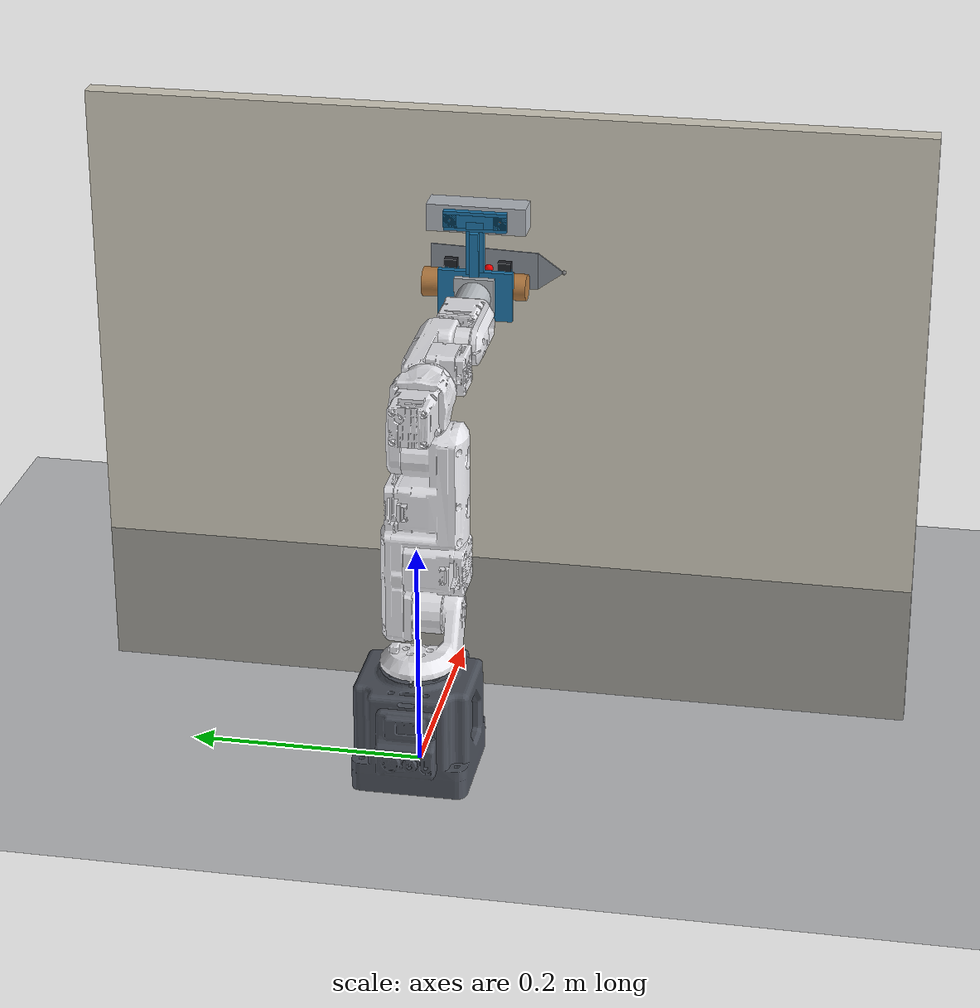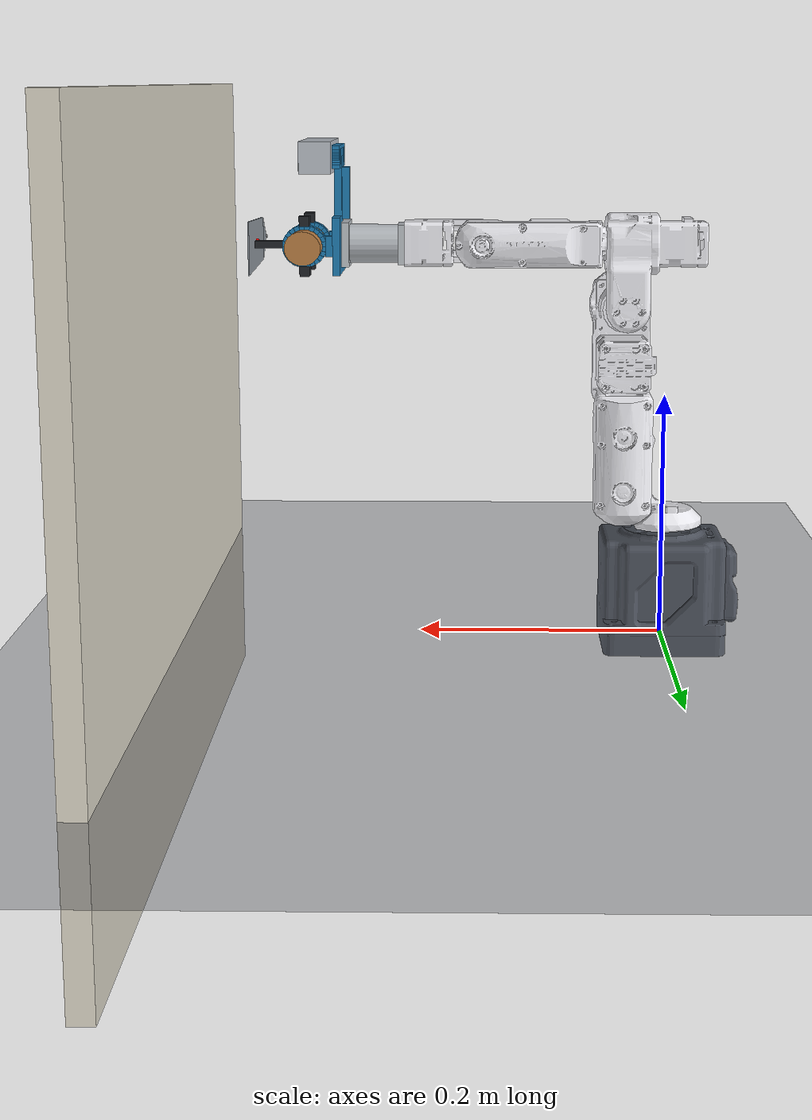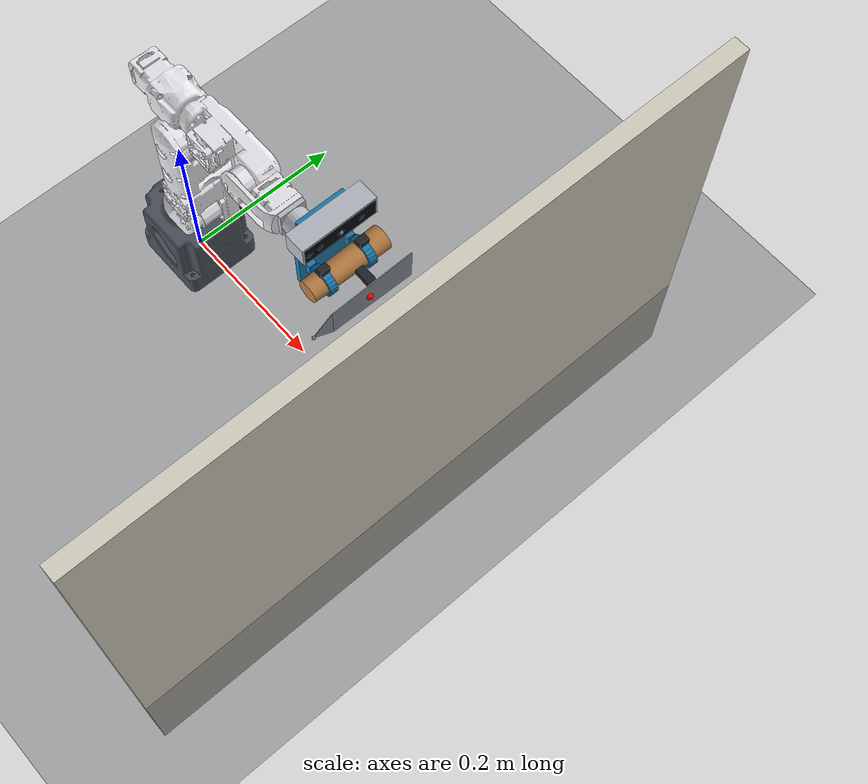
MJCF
<mujoco model="dummy_wall_trowel_SIM_ASSUMPTIONS_NOT_CALIBRATED">
  <!-- 由 tools/modeling/build_dummy_v2.py 生成，请勿手改。运动学 = V2 固件 DH；质量/惯量 = CAD 体积×估计密度 + 资料质量；执行器 = 资料额定值推算。均未经实机辨识。 -->
  <compiler angle="radian" meshdir="../../models/meshes_v2/" boundinertia="1e-07"/>

  <option integrator="implicitfast"/>

  <visual>
    <global offwidth="960" offheight="720"/>
  </visual>

  <default>
    <geom contype="0" conaffinity="0"/>
  </default>

  <asset>
    <mesh name="base_link" file="base_link.stl" scale="0.001 0.001 0.001" inertia="shell"/>
    <mesh name="link1" file="link1.stl" scale="0.001 0.001 0.001" inertia="shell"/>
    <mesh name="link2" file="link2.stl" scale="0.001 0.001 0.001" inertia="shell"/>
    <mesh name="link3" file="link3.stl" scale="0.001 0.001 0.001" inertia="shell"/>
    <mesh name="link4" file="link4.stl" scale="0.001 0.001 0.001" inertia="shell"/>
    <mesh name="link5" file="link5.stl" scale="0.001 0.001 0.001" inertia="shell"/>
    <mesh name="link6" file="link6.stl" scale="0.001 0.001 0.001" inertia="shell"/>
    <mesh name="handle_geom_mesh" vertex="0.0426612 0.041 0 0.0426612 0.0408909 0.00156631 0.0426612 0.0405656 0.00310583 0.0426612 0.0400295 0.0045922 0.0426612 0.0392918 0.006 0.0426612 0.0383653 0.00730514 0.0426612 0.0372656 0.00848528 0.0426612 0.0360117 0.00952024 0.0426612 0.034625 0.0103923 0.0426612 0.0331292 0.0110866 0.0426612 0.0315499 0.0115911 0.0426612 0.0299142 0.0118973 0.0426612 0.02825 0.012 0.0426612 0.0265858 0.0118973 0.0426612 0.0249501 0.0115911 0.0426612 0.0233708 0.0110866 0.0426612 0.021875 0.0103923 0.0426612 0.0204883 0.00952024 0.0426612 0.0192344 0.00848528 0.0426612 0.0181347 0.00730514 0.0426612 0.0172082 0.006 0.0426612 0.0164705 0.0045922 0.0426612 0.0159344 0.00310583 0.0426612 0.0156091 0.00156631 0.0426612 0.0155 1.46958e-18 0.0426612 0.0156091 -0.00156631 0.0426612 0.0159344 -0.00310583 0.0426612 0.0164705 -0.0045922 0.0426612 0.0172082 -0.006 0.0426612 0.0181347 -0.00730514 0.0426612 0.0192344 -0.00848528 0.0426612 0.0204883 -0.00952024 0.0426612 0.021875 -0.0103923 0.0426612 0.0233708 -0.0110866 0.0426612 0.0249501 -0.0115911 0.0426612 0.0265858 -0.0118973 0.0426612 0.02825 -0.012 0.0426612 0.0299142 -0.0118973 0.0426612 0.0315499 -0.0115911 0.0426612 0.0331292 -0.0110866 0.0426612 0.034625 -0.0103923 0.0426612 0.0360117 -0.00952024 0.0426612 0.0372656 -0.00848528 0.0426612 0.0383653 -0.00730514 0.0426612 0.0392918 -0.006 0.0426612 0.0400295 -0.0045922 0.0426612 0.0405656 -0.00310583 0.0426612 0.0408909 -0.00156631 -0.0523388 0.0425 0 -0.0523388 0.0423781 0.00172947 -0.0523388 0.0420144 0.00342935 -0.0523388 0.0414153 0.00507056 -0.0523388 0.0405909 0.006625 -0.0523388 0.0395553 0.00806609 -0.0523388 0.0383263 0.00936916 -0.0523388 0.0369249 0.0105119 -0.0523388 0.035375 0.0114748 -0.0523388 0.0337032 0.0122414 -0.0523388 0.0319382 0.0127985 -0.0523388 0.03011 0.0131366 -0.0523388 0.02825 0.01325 -0.0523388 0.02639 0.0131366 -0.0523388 0.0245618 0.0127985 -0.0523388 0.0227968 0.0122414 -0.0523388 0.021125 0.0114748 -0.0523388 0.0195751 0.0105119 -0.0523388 0.0181737 0.00936916 -0.0523388 0.0169447 0.00806609 -0.0523388 0.0159091 0.006625 -0.0523388 0.0150847 0.00507056 -0.0523388 0.0144856 0.00342935 -0.0523388 0.0141219 0.00172947 -0.0523388 0.014 1.62266e-18 -0.0523388 0.0141219 -0.00172947 -0.0523388 0.0144856 -0.00342935 -0.0523388 0.0150847 -0.00507056 -0.0523388 0.0159091 -0.006625 -0.0523388 0.0169447 -0.00806609 -0.0523388 0.0181737 -0.00936916 -0.0523388 0.0195751 -0.0105119 -0.0523388 0.021125 -0.0114748 -0.0523388 0.0227968 -0.0122414 -0.0523388 0.0245618 -0.0127985 -0.0523388 0.02639 -0.0131366 -0.0523388 0.02825 -0.01325 -0.0523388 0.03011 -0.0131366 -0.0523388 0.0319382 -0.0127985 -0.0523388 0.0337032 -0.0122414 -0.0523388 0.035375 -0.0114748 -0.0523388 0.0369249 -0.0105119 -0.0523388 0.0383263 -0.00936916 -0.0523388 0.0395553 -0.00806609 -0.0523388 0.0405909 -0.006625 -0.0523388 0.0414153 -0.00507056 -0.0523388 0.0420144 -0.00342935 -0.0523388 0.0423781 -0.00172947"/>
    <mesh name="clamp_0_0_mesh" vertex="-0.0315 0.0423999 0 -0.0315 0.0419178 0.00342071 -0.0315 0.0458999 0 -0.0315 0.0452985 0.00432657 -0.0225 0.0423999 0 -0.0225 0.0419178 0.00342071 -0.0225 0.0458999 0 -0.0225 0.0452985 0.00432657"/>
    <mesh name="clamp_0_1_mesh" vertex="-0.0315 0.0419178 0.00342071 -0.0315 0.0405042 0.0066083 -0.0315 0.0452985 0.00432657 -0.0315 0.0435353 0.0083583 -0.0225 0.0419178 0.00342071 -0.0225 0.0405042 0.0066083 -0.0225 0.0452985 0.00432657 -0.0225 0.0435353 0.0083583"/>
    <mesh name="clamp_0_2_mesh" vertex="-0.0315 0.0405042 0.0066083 -0.0315 0.0382555 0.00934554 -0.0315 0.0435353 0.0083583 -0.0315 0.0407304 0.0118204 -0.0225 0.0405042 0.0066083 -0.0225 0.0382555 0.00934554 -0.0225 0.0435353 0.0083583 -0.0225 0.0407304 0.0118204"/>
    <mesh name="clamp_0_3_mesh" vertex="-0.0315 0.0382555 0.00934554 -0.0315 0.035325 0.0114459 -0.0315 0.0407304 0.0118204 -0.0315 0.037075 0.014477 -0.0225 0.0382555 0.00934554 -0.0225 0.035325 0.0114459 -0.0225 0.0407304 0.0118204 -0.0225 0.037075 0.014477"/>
    <mesh name="clamp_0_4_mesh" vertex="-0.0315 0.035325 0.0114459 -0.0315 0.0319123 0.0127663 -0.0315 0.037075 0.014477 -0.0315 0.0328181 0.016147 -0.0225 0.035325 0.0114459 -0.0225 0.0319123 0.0127663 -0.0225 0.037075 0.014477 -0.0225 0.0328181 0.016147"/>
    <mesh name="clamp_0_5_mesh" vertex="-0.0315 0.0319123 0.0127663 -0.0315 0.0284198 0.0132156 -0.0315 0.0328181 0.016147 -0.0315 0.0284618 0.0167154 -0.0225 0.0319123 0.0127663 -0.0225 0.0284198 0.0132156 -0.0225 0.0328181 0.016147 -0.0225 0.0284618 0.0167154"/>
    <mesh name="clamp_0_6_mesh" vertex="-0.0315 0.0280802 0.0132156 -0.0315 0.0245877 0.0127663 -0.0315 0.0280382 0.0167154 -0.0315 0.0236819 0.016147 -0.0225 0.0280802 0.0132156 -0.0225 0.0245877 0.0127663 -0.0225 0.0280382 0.0167154 -0.0225 0.0236819 0.016147"/>
    <mesh name="clamp_0_7_mesh" vertex="-0.0315 0.0245877 0.0127663 -0.0315 0.021175 0.0114459 -0.0315 0.0236819 0.016147 -0.0315 0.019425 0.014477 -0.0225 0.0245877 0.0127663 -0.0225 0.021175 0.0114459 -0.0225 0.0236819 0.016147 -0.0225 0.019425 0.014477"/>
    <mesh name="clamp_0_8_mesh" vertex="-0.0315 0.021175 0.0114459 -0.0315 0.0182445 0.00934554 -0.0315 0.019425 0.014477 -0.0315 0.0157696 0.0118204 -0.0225 0.021175 0.0114459 -0.0225 0.0182445 0.00934554 -0.0225 0.019425 0.014477 -0.0225 0.0157696 0.0118204"/>
    <mesh name="clamp_0_9_mesh" vertex="-0.0315 0.0182445 0.00934554 -0.0315 0.0159958 0.0066083 -0.0315 0.0157696 0.0118204 -0.0315 0.0129647 0.0083583 -0.0225 0.0182445 0.00934554 -0.0225 0.0159958 0.0066083 -0.0225 0.0157696 0.0118204 -0.0225 0.0129647 0.0083583"/>
    <mesh name="clamp_0_10_mesh" vertex="-0.0315 0.0159958 0.0066083 -0.0315 0.0145822 0.00342071 -0.0315 0.0129647 0.0083583 -0.0315 0.0112015 0.00432657 -0.0225 0.0159958 0.0066083 -0.0225 0.0145822 0.00342071 -0.0225 0.0129647 0.0083583 -0.0225 0.0112015 0.00432657"/>
    <mesh name="clamp_0_11_mesh" vertex="-0.0315 0.0145822 0.00342071 -0.0315 0.0141001 1.61857e-18 -0.0315 0.0112015 0.00432657 -0.0315 0.0106001 2.04719e-18 -0.0225 0.0145822 0.00342071 -0.0225 0.0141001 1.61857e-18 -0.0225 0.0112015 0.00432657 -0.0225 0.0106001 2.04719e-18"/>
    <mesh name="clamp_0_12_mesh" vertex="-0.0315 0.0141001 1.61857e-18 -0.0315 0.0145822 -0.00342071 -0.0315 0.0106001 2.04719e-18 -0.0315 0.0112015 -0.00432657 -0.0225 0.0141001 1.61857e-18 -0.0225 0.0145822 -0.00342071 -0.0225 0.0106001 2.04719e-18 -0.0225 0.0112015 -0.00432657"/>
    <mesh name="clamp_0_13_mesh" vertex="-0.0315 0.0145822 -0.00342071 -0.0315 0.0159958 -0.0066083 -0.0315 0.0112015 -0.00432657 -0.0315 0.0129647 -0.0083583 -0.0225 0.0145822 -0.00342071 -0.0225 0.0159958 -0.0066083 -0.0225 0.0112015 -0.00432657 -0.0225 0.0129647 -0.0083583"/>
    <mesh name="clamp_0_14_mesh" vertex="-0.0315 0.0159958 -0.0066083 -0.0315 0.0182445 -0.00934554 -0.0315 0.0129647 -0.0083583 -0.0315 0.0157696 -0.0118204 -0.0225 0.0159958 -0.0066083 -0.0225 0.0182445 -0.00934554 -0.0225 0.0129647 -0.0083583 -0.0225 0.0157696 -0.0118204"/>
    <mesh name="clamp_0_15_mesh" vertex="-0.0315 0.0182445 -0.00934554 -0.0315 0.021175 -0.0114459 -0.0315 0.0157696 -0.0118204 -0.0315 0.019425 -0.014477 -0.0225 0.0182445 -0.00934554 -0.0225 0.021175 -0.0114459 -0.0225 0.0157696 -0.0118204 -0.0225 0.019425 -0.014477"/>
    <mesh name="clamp_0_16_mesh" vertex="-0.0315 0.021175 -0.0114459 -0.0315 0.0245877 -0.0127663 -0.0315 0.019425 -0.014477 -0.0315 0.0236819 -0.016147 -0.0225 0.021175 -0.0114459 -0.0225 0.0245877 -0.0127663 -0.0225 0.019425 -0.014477 -0.0225 0.0236819 -0.016147"/>
    <mesh name="clamp_0_17_mesh" vertex="-0.0315 0.0245877 -0.0127663 -0.0315 0.0280802 -0.0132156 -0.0315 0.0236819 -0.016147 -0.0315 0.0280382 -0.0167154 -0.0225 0.0245877 -0.0127663 -0.0225 0.0280802 -0.0132156 -0.0225 0.0236819 -0.016147 -0.0225 0.0280382 -0.0167154"/>
    <mesh name="clamp_0_18_mesh" vertex="-0.0315 0.0284198 -0.0132156 -0.0315 0.0319123 -0.0127663 -0.0315 0.0284618 -0.0167154 -0.0315 0.0328181 -0.016147 -0.0225 0.0284198 -0.0132156 -0.0225 0.0319123 -0.0127663 -0.0225 0.0284618 -0.0167154 -0.0225 0.0328181 -0.016147"/>
    <mesh name="clamp_0_19_mesh" vertex="-0.0315 0.0319123 -0.0127663 -0.0315 0.035325 -0.0114459 -0.0315 0.0328181 -0.016147 -0.0315 0.037075 -0.014477 -0.0225 0.0319123 -0.0127663 -0.0225 0.035325 -0.0114459 -0.0225 0.0328181 -0.016147 -0.0225 0.037075 -0.014477"/>
    <mesh name="clamp_0_20_mesh" vertex="-0.0315 0.035325 -0.0114459 -0.0315 0.0382555 -0.00934554 -0.0315 0.037075 -0.014477 -0.0315 0.0407304 -0.0118204 -0.0225 0.035325 -0.0114459 -0.0225 0.0382555 -0.00934554 -0.0225 0.037075 -0.014477 -0.0225 0.0407304 -0.0118204"/>
    <mesh name="clamp_0_21_mesh" vertex="-0.0315 0.0382555 -0.00934554 -0.0315 0.0405042 -0.0066083 -0.0315 0.0407304 -0.0118204 -0.0315 0.0435353 -0.0083583 -0.0225 0.0382555 -0.00934554 -0.0225 0.0405042 -0.0066083 -0.0225 0.0407304 -0.0118204 -0.0225 0.0435353 -0.0083583"/>
    <mesh name="clamp_0_22_mesh" vertex="-0.0315 0.0405042 -0.0066083 -0.0315 0.0419178 -0.00342071 -0.0315 0.0435353 -0.0083583 -0.0315 0.0452985 -0.00432657 -0.0225 0.0405042 -0.0066083 -0.0225 0.0419178 -0.00342071 -0.0225 0.0435353 -0.0083583 -0.0225 0.0452985 -0.00432657"/>
    <mesh name="clamp_0_23_mesh" vertex="-0.0315 0.0419178 -0.00342071 -0.0315 0.0423999 -3.23713e-18 -0.0315 0.0452985 -0.00432657 -0.0315 0.0458999 -4.09438e-18 -0.0225 0.0419178 -0.00342071 -0.0225 0.0423999 -3.23713e-18 -0.0225 0.0452985 -0.00432657 -0.0225 0.0458999 -4.09438e-18"/>
    <mesh name="clamp_1_0_mesh" vertex="0.0175 0.0416262 0 0.0175 0.0411704 0.00325384 0.0175 0.0451262 0 0.0175 0.0445512 0.0041597 0.0265 0.0416262 0 0.0265 0.0411704 0.00325384 0.0265 0.0451262 0 0.0265 0.0445512 0.0041597"/>
    <mesh name="clamp_1_1_mesh" vertex="0.0175 0.0411704 0.00325384 0.0175 0.0398342 0.00628593 0.0175 0.0445512 0.0041597 0.0175 0.0428652 0.00803593 0.0265 0.0411704 0.00325384 0.0265 0.0398342 0.00628593 0.0265 0.0445512 0.0041597 0.0265 0.0428652 0.00803593"/>
    <mesh name="clamp_1_2_mesh" vertex="0.0175 0.0398342 0.00628593 0.0175 0.0377084 0.00888965 0.0175 0.0428652 0.00803593 0.0175 0.0401833 0.0113645 0.0265 0.0398342 0.00628593 0.0265 0.0377084 0.00888965 0.0265 0.0428652 0.00803593 0.0265 0.0401833 0.0113645"/>
    <mesh name="clamp_1_3_mesh" vertex="0.0175 0.0377084 0.00888965 0.0175 0.0349381 0.0108875 0.0175 0.0401833 0.0113645 0.0175 0.0366881 0.0139186 0.0265 0.0377084 0.00888965 0.0265 0.0349381 0.0108875 0.0265 0.0401833 0.0113645 0.0265 0.0366881 0.0139186"/>
    <mesh name="clamp_1_4_mesh" vertex="0.0175 0.0349381 0.0108875 0.0175 0.031712 0.0121435 0.0175 0.0366881 0.0139186 0.0175 0.0326179 0.0155242 0.0265 0.0349381 0.0108875 0.0265 0.031712 0.0121435 0.0265 0.0366881 0.0139186 0.0265 0.0326179 0.0155242"/>
    <mesh name="clamp_1_5_mesh" vertex="0.0175 0.031712 0.0121435 0.0175 0.0284105 0.012571 0.0175 0.0326179 0.0155242 0.0175 0.0284525 0.0160707 0.0265 0.031712 0.0121435 0.0265 0.0284105 0.012571 0.0265 0.0326179 0.0155242 0.0265 0.0284525 0.0160707"/>
    <mesh name="clamp_1_6_mesh" vertex="0.0175 0.0280895 0.012571 0.0175 0.024788 0.0121435 0.0175 0.0280475 0.0160707 0.0175 0.0238821 0.0155242 0.0265 0.0280895 0.012571 0.0265 0.024788 0.0121435 0.0265 0.0280475 0.0160707 0.0265 0.0238821 0.0155242"/>
    <mesh name="clamp_1_7_mesh" vertex="0.0175 0.024788 0.0121435 0.0175 0.0215619 0.0108875 0.0175 0.0238821 0.0155242 0.0175 0.0198119 0.0139186 0.0265 0.024788 0.0121435 0.0265 0.0215619 0.0108875 0.0265 0.0238821 0.0155242 0.0265 0.0198119 0.0139186"/>
    <mesh name="clamp_1_8_mesh" vertex="0.0175 0.0215619 0.0108875 0.0175 0.0187916 0.00888965 0.0175 0.0198119 0.0139186 0.0175 0.0163167 0.0113645 0.0265 0.0215619 0.0108875 0.0265 0.0187916 0.00888965 0.0265 0.0198119 0.0139186 0.0265 0.0163167 0.0113645"/>
    <mesh name="clamp_1_9_mesh" vertex="0.0175 0.0187916 0.00888965 0.0175 0.0166658 0.00628593 0.0175 0.0163167 0.0113645 0.0175 0.0136348 0.00803593 0.0265 0.0187916 0.00888965 0.0265 0.0166658 0.00628593 0.0265 0.0163167 0.0113645 0.0265 0.0136348 0.00803593"/>
    <mesh name="clamp_1_10_mesh" vertex="0.0175 0.0166658 0.00628593 0.0175 0.0153296 0.00325384 0.0175 0.0136348 0.00803593 0.0175 0.0119488 0.0041597 0.0265 0.0166658 0.00628593 0.0265 0.0153296 0.00325384 0.0265 0.0136348 0.00803593 0.0265 0.0119488 0.0041597"/>
    <mesh name="clamp_1_11_mesh" vertex="0.0175 0.0153296 0.00325384 0.0175 0.0148738 1.53961e-18 0.0175 0.0119488 0.0041597 0.0175 0.0113738 1.96823e-18 0.0265 0.0153296 0.00325384 0.0265 0.0148738 1.53961e-18 0.0265 0.0119488 0.0041597 0.0265 0.0113738 1.96823e-18"/>
    <mesh name="clamp_1_12_mesh" vertex="0.0175 0.0148738 1.53961e-18 0.0175 0.0153296 -0.00325384 0.0175 0.0113738 1.96823e-18 0.0175 0.0119488 -0.0041597 0.0265 0.0148738 1.53961e-18 0.0265 0.0153296 -0.00325384 0.0265 0.0113738 1.96823e-18 0.0265 0.0119488 -0.0041597"/>
    <mesh name="clamp_1_13_mesh" vertex="0.0175 0.0153296 -0.00325384 0.0175 0.0166658 -0.00628593 0.0175 0.0119488 -0.0041597 0.0175 0.0136348 -0.00803593 0.0265 0.0153296 -0.00325384 0.0265 0.0166658 -0.00628593 0.0265 0.0119488 -0.0041597 0.0265 0.0136348 -0.00803593"/>
    <mesh name="clamp_1_14_mesh" vertex="0.0175 0.0166658 -0.00628593 0.0175 0.0187916 -0.00888965 0.0175 0.0136348 -0.00803593 0.0175 0.0163167 -0.0113645 0.0265 0.0166658 -0.00628593 0.0265 0.0187916 -0.00888965 0.0265 0.0136348 -0.00803593 0.0265 0.0163167 -0.0113645"/>
    <mesh name="clamp_1_15_mesh" vertex="0.0175 0.0187916 -0.00888965 0.0175 0.0215619 -0.0108875 0.0175 0.0163167 -0.0113645 0.0175 0.0198119 -0.0139186 0.0265 0.0187916 -0.00888965 0.0265 0.0215619 -0.0108875 0.0265 0.0163167 -0.0113645 0.0265 0.0198119 -0.0139186"/>
    <mesh name="clamp_1_16_mesh" vertex="0.0175 0.0215619 -0.0108875 0.0175 0.024788 -0.0121435 0.0175 0.0198119 -0.0139186 0.0175 0.0238821 -0.0155242 0.0265 0.0215619 -0.0108875 0.0265 0.024788 -0.0121435 0.0265 0.0198119 -0.0139186 0.0265 0.0238821 -0.0155242"/>
    <mesh name="clamp_1_17_mesh" vertex="0.0175 0.024788 -0.0121435 0.0175 0.0280895 -0.012571 0.0175 0.0238821 -0.0155242 0.0175 0.0280475 -0.0160707 0.0265 0.024788 -0.0121435 0.0265 0.0280895 -0.012571 0.0265 0.0238821 -0.0155242 0.0265 0.0280475 -0.0160707"/>
    <mesh name="clamp_1_18_mesh" vertex="0.0175 0.0284105 -0.012571 0.0175 0.031712 -0.0121435 0.0175 0.0284525 -0.0160707 0.0175 0.0326179 -0.0155242 0.0265 0.0284105 -0.012571 0.0265 0.031712 -0.0121435 0.0265 0.0284525 -0.0160707 0.0265 0.0326179 -0.0155242"/>
    <mesh name="clamp_1_19_mesh" vertex="0.0175 0.031712 -0.0121435 0.0175 0.0349381 -0.0108875 0.0175 0.0326179 -0.0155242 0.0175 0.0366881 -0.0139186 0.0265 0.031712 -0.0121435 0.0265 0.0349381 -0.0108875 0.0265 0.0326179 -0.0155242 0.0265 0.0366881 -0.0139186"/>
    <mesh name="clamp_1_20_mesh" vertex="0.0175 0.0349381 -0.0108875 0.0175 0.0377084 -0.00888965 0.0175 0.0366881 -0.0139186 0.0175 0.0401833 -0.0113645 0.0265 0.0349381 -0.0108875 0.0265 0.0377084 -0.00888965 0.0265 0.0366881 -0.0139186 0.0265 0.0401833 -0.0113645"/>
    <mesh name="clamp_1_21_mesh" vertex="0.0175 0.0377084 -0.00888965 0.0175 0.0398342 -0.00628593 0.0175 0.0401833 -0.0113645 0.0175 0.0428652 -0.00803593 0.0265 0.0377084 -0.00888965 0.0265 0.0398342 -0.00628593 0.0265 0.0401833 -0.0113645 0.0265 0.0428652 -0.00803593"/>
    <mesh name="clamp_1_22_mesh" vertex="0.0175 0.0398342 -0.00628593 0.0175 0.0411704 -0.00325384 0.0175 0.0428652 -0.00803593 0.0175 0.0445512 -0.0041597 0.0265 0.0398342 -0.00628593 0.0265 0.0411704 -0.00325384 0.0265 0.0428652 -0.00803593 0.0265 0.0445512 -0.0041597"/>
    <mesh name="clamp_1_23_mesh" vertex="0.0175 0.0411704 -0.00325384 0.0175 0.0416262 -3.07922e-18 0.0175 0.0445512 -0.0041597 0.0175 0.0451262 -3.93647e-18 0.0265 0.0411704 -0.00325384 0.0265 0.0416262 -3.07922e-18 0.0265 0.0445512 -0.0041597 0.0265 0.0451262 -3.93647e-18"/>
    <mesh name="blade_geom_mesh" vertex="-0.0543388 0 -0.021 0.0456612 0 -0.0175 0.0456612 0 0.0175 -0.0543388 0 0.021 -0.0543388 0.001 -0.021 0.0456612 0.001 -0.0175 0.0456612 0.001 0.0175 -0.0543388 0.001 0.021"/>
    <mesh name="blade_tip_geom_mesh" vertex="0.0456612 0 -0.0175 0.0696612 0 0 0.0456612 0 0.0175 0.0456612 0.001 -0.0175 0.0696612 0.001 0 0.0456612 0.001 0.0175"/>
    <mesh name="camera_bore_0_0_mesh" vertex="-0.0209 0 0.07 -0.0209307 0 0.0703121 -0.0165 0 0.07 -0.0165 0 0.0711935 -0.0209 0.006 0.07 -0.0209307 0.006 0.0703121 -0.0165 0.006 0.07 -0.0165 0.006 0.0711935"/>
    <mesh name="camera_bore_0_1_mesh" vertex="-0.0209307 0 0.0703121 -0.0210218 0 0.0706123 -0.0165 0 0.0711935 -0.0165 0 0.0724853 -0.0209307 0.006 0.0703121 -0.0210218 0.006 0.0706123 -0.0165 0.006 0.0711935 -0.0165 0.006 0.0724853"/>
    <mesh name="camera_bore_0_2_mesh" vertex="-0.0210218 0 0.0706123 -0.0211696 0 0.0708889 -0.0165 0 0.0724853 -0.0165 0 0.0740091 -0.0210218 0.006 0.0706123 -0.0211696 0.006 0.0708889 -0.0165 0.006 0.0724853 -0.0165 0.006 0.0740091"/>
    <mesh name="camera_bore_0_3_mesh" vertex="-0.0211696 0 0.0708889 -0.0213686 0 0.0711314 -0.0165 0 0.0740091 -0.0165 0 0.076 -0.0211696 0.006 0.0708889 -0.0213686 0.006 0.0711314 -0.0165 0.006 0.0740091 -0.0165 0.006 0.076"/>
    <mesh name="camera_bore_0_4_mesh" vertex="-0.0213686 0 0.0711314 -0.0216111 0 0.0713304 -0.0165 0 0.076 -0.0184909 0 0.076 -0.0213686 0.006 0.0711314 -0.0216111 0.006 0.0713304 -0.0165 0.006 0.076 -0.0184909 0.006 0.076"/>
    <mesh name="camera_bore_0_5_mesh" vertex="-0.0216111 0 0.0713304 -0.0218877 0 0.0714782 -0.0184909 0 0.076 -0.0200147 0 0.076 -0.0216111 0.006 0.0713304 -0.0218877 0.006 0.0714782 -0.0184909 0.006 0.076 -0.0200147 0.006 0.076"/>
    <mesh name="camera_bore_0_6_mesh" vertex="-0.0218877 0 0.0714782 -0.0221879 0 0.0715693 -0.0200147 0 0.076 -0.0213065 0 0.076 -0.0218877 0.006 0.0714782 -0.0221879 0.006 0.0715693 -0.0200147 0.006 0.076 -0.0213065 0.006 0.076"/>
    <mesh name="camera_bore_0_7_mesh" vertex="-0.0221879 0 0.0715693 -0.0225 0 0.0716 -0.0213065 0 0.076 -0.0225 0 0.076 -0.0221879 0.006 0.0715693 -0.0225 0.006 0.0716 -0.0213065 0.006 0.076 -0.0225 0.006 0.076"/>
    <mesh name="camera_bore_0_8_mesh" vertex="-0.0225 0 0.0716 -0.0228121 0 0.0715693 -0.0225 0 0.076 -0.0236935 0 0.076 -0.0225 0.006 0.0716 -0.0228121 0.006 0.0715693 -0.0225 0.006 0.076 -0.0236935 0.006 0.076"/>
    <mesh name="camera_bore_0_9_mesh" vertex="-0.0228121 0 0.0715693 -0.0231123 0 0.0714782 -0.0236935 0 0.076 -0.0249853 0 0.076 -0.0228121 0.006 0.0715693 -0.0231123 0.006 0.0714782 -0.0236935 0.006 0.076 -0.0249853 0.006 0.076"/>
    <mesh name="camera_bore_0_10_mesh" vertex="-0.0231123 0 0.0714782 -0.0233889 0 0.0713304 -0.0249853 0 0.076 -0.0265091 0 0.076 -0.0231123 0.006 0.0714782 -0.0233889 0.006 0.0713304 -0.0249853 0.006 0.076 -0.0265091 0.006 0.076"/>
    <mesh name="camera_bore_0_11_mesh" vertex="-0.0233889 0 0.0713304 -0.0236314 0 0.0711314 -0.0265091 0 0.076 -0.0285 0 0.076 -0.0233889 0.006 0.0713304 -0.0236314 0.006 0.0711314 -0.0265091 0.006 0.076 -0.0285 0.006 0.076"/>
    <mesh name="camera_bore_0_12_mesh" vertex="-0.0236314 0 0.0711314 -0.0238304 0 0.0708889 -0.0285 0 0.076 -0.0285 0 0.0740091 -0.0236314 0.006 0.0711314 -0.0238304 0.006 0.0708889 -0.0285 0.006 0.076 -0.0285 0.006 0.0740091"/>
    <mesh name="camera_bore_0_13_mesh" vertex="-0.0238304 0 0.0708889 -0.0239782 0 0.0706123 -0.0285 0 0.0740091 -0.0285 0 0.0724853 -0.0238304 0.006 0.0708889 -0.0239782 0.006 0.0706123 -0.0285 0.006 0.0740091 -0.0285 0.006 0.0724853"/>
    <mesh name="camera_bore_0_14_mesh" vertex="-0.0239782 0 0.0706123 -0.0240693 0 0.0703121 -0.0285 0 0.0724853 -0.0285 0 0.0711935 -0.0239782 0.006 0.0706123 -0.0240693 0.006 0.0703121 -0.0285 0.006 0.0724853 -0.0285 0.006 0.0711935"/>
    <mesh name="camera_bore_0_15_mesh" vertex="-0.0240693 0 0.0703121 -0.0241 0 0.07 -0.0285 0 0.0711935 -0.0285 0 0.07 -0.0240693 0.006 0.0703121 -0.0241 0.006 0.07 -0.0285 0.006 0.0711935 -0.0285 0.006 0.07"/>
    <mesh name="camera_bore_0_16_mesh" vertex="-0.0241 0 0.07 -0.0240693 0 0.0696879 -0.0285 0 0.07 -0.0285 0 0.0688065 -0.0241 0.006 0.07 -0.0240693 0.006 0.0696879 -0.0285 0.006 0.07 -0.0285 0.006 0.0688065"/>
    <mesh name="camera_bore_0_17_mesh" vertex="-0.0240693 0 0.0696879 -0.0239782 0 0.0693877 -0.0285 0 0.0688065 -0.0285 0 0.0675147 -0.0240693 0.006 0.0696879 -0.0239782 0.006 0.0693877 -0.0285 0.006 0.0688065 -0.0285 0.006 0.0675147"/>
    <mesh name="camera_bore_0_18_mesh" vertex="-0.0239782 0 0.0693877 -0.0238304 0 0.0691111 -0.0285 0 0.0675147 -0.0285 0 0.0659909 -0.0239782 0.006 0.0693877 -0.0238304 0.006 0.0691111 -0.0285 0.006 0.0675147 -0.0285 0.006 0.0659909"/>
    <mesh name="camera_bore_0_19_mesh" vertex="-0.0238304 0 0.0691111 -0.0236314 0 0.0688686 -0.0285 0 0.0659909 -0.0285 0 0.064 -0.0238304 0.006 0.0691111 -0.0236314 0.006 0.0688686 -0.0285 0.006 0.0659909 -0.0285 0.006 0.064"/>
    <mesh name="camera_bore_0_20_mesh" vertex="-0.0236314 0 0.0688686 -0.0233889 0 0.0686696 -0.0285 0 0.064 -0.0265091 0 0.064 -0.0236314 0.006 0.0688686 -0.0233889 0.006 0.0686696 -0.0285 0.006 0.064 -0.0265091 0.006 0.064"/>
    <mesh name="camera_bore_0_21_mesh" vertex="-0.0233889 0 0.0686696 -0.0231123 0 0.0685218 -0.0265091 0 0.064 -0.0249853 0 0.064 -0.0233889 0.006 0.0686696 -0.0231123 0.006 0.0685218 -0.0265091 0.006 0.064 -0.0249853 0.006 0.064"/>
    <mesh name="camera_bore_0_22_mesh" vertex="-0.0231123 0 0.0685218 -0.0228121 0 0.0684307 -0.0249853 0 0.064 -0.0236935 0 0.064 -0.0231123 0.006 0.0685218 -0.0228121 0.006 0.0684307 -0.0249853 0.006 0.064 -0.0236935 0.006 0.064"/>
    <mesh name="camera_bore_0_23_mesh" vertex="-0.0228121 0 0.0684307 -0.0225 0 0.0684 -0.0236935 0 0.064 -0.0225 0 0.064 -0.0228121 0.006 0.0684307 -0.0225 0.006 0.0684 -0.0236935 0.006 0.064 -0.0225 0.006 0.064"/>
    <mesh name="camera_bore_0_24_mesh" vertex="-0.0225 0 0.0684 -0.0221879 0 0.0684307 -0.0225 0 0.064 -0.0213065 0 0.064 -0.0225 0.006 0.0684 -0.0221879 0.006 0.0684307 -0.0225 0.006 0.064 -0.0213065 0.006 0.064"/>
    <mesh name="camera_bore_0_25_mesh" vertex="-0.0221879 0 0.0684307 -0.0218877 0 0.0685218 -0.0213065 0 0.064 -0.0200147 0 0.064 -0.0221879 0.006 0.0684307 -0.0218877 0.006 0.0685218 -0.0213065 0.006 0.064 -0.0200147 0.006 0.064"/>
    <mesh name="camera_bore_0_26_mesh" vertex="-0.0218877 0 0.0685218 -0.0216111 0 0.0686696 -0.0200147 0 0.064 -0.0184909 0 0.064 -0.0218877 0.006 0.0685218 -0.0216111 0.006 0.0686696 -0.0200147 0.006 0.064 -0.0184909 0.006 0.064"/>
    <mesh name="camera_bore_0_27_mesh" vertex="-0.0216111 0 0.0686696 -0.0213686 0 0.0688686 -0.0184909 0 0.064 -0.0165 0 0.064 -0.0216111 0.006 0.0686696 -0.0213686 0.006 0.0688686 -0.0184909 0.006 0.064 -0.0165 0.006 0.064"/>
    <mesh name="camera_bore_0_28_mesh" vertex="-0.0213686 0 0.0688686 -0.0211696 0 0.0691111 -0.0165 0 0.064 -0.0165 0 0.0659909 -0.0213686 0.006 0.0688686 -0.0211696 0.006 0.0691111 -0.0165 0.006 0.064 -0.0165 0.006 0.0659909"/>
    <mesh name="camera_bore_0_29_mesh" vertex="-0.0211696 0 0.0691111 -0.0210218 0 0.0693877 -0.0165 0 0.0659909 -0.0165 0 0.0675147 -0.0211696 0.006 0.0691111 -0.0210218 0.006 0.0693877 -0.0165 0.006 0.0659909 -0.0165 0.006 0.0675147"/>
    <mesh name="camera_bore_0_30_mesh" vertex="-0.0210218 0 0.0693877 -0.0209307 0 0.0696879 -0.0165 0 0.0675147 -0.0165 0 0.0688065 -0.0210218 0.006 0.0693877 -0.0209307 0.006 0.0696879 -0.0165 0.006 0.0675147 -0.0165 0.006 0.0688065"/>
    <mesh name="camera_bore_0_31_mesh" vertex="-0.0209307 0 0.0696879 -0.0209 0 0.07 -0.0165 0 0.0688065 -0.0165 0 0.07 -0.0209307 0.006 0.0696879 -0.0209 0.006 0.07 -0.0165 0.006 0.0688065 -0.0165 0.006 0.07"/>
    <mesh name="camera_bore_1_0_mesh" vertex="0.0241 0 0.07 0.0240693 0 0.0703121 0.0285 0 0.07 0.0285 0 0.0711935 0.0241 0.006 0.07 0.0240693 0.006 0.0703121 0.0285 0.006 0.07 0.0285 0.006 0.0711935"/>
    <mesh name="camera_bore_1_1_mesh" vertex="0.0240693 0 0.0703121 0.0239782 0 0.0706123 0.0285 0 0.0711935 0.0285 0 0.0724853 0.0240693 0.006 0.0703121 0.0239782 0.006 0.0706123 0.0285 0.006 0.0711935 0.0285 0.006 0.0724853"/>
    <mesh name="camera_bore_1_2_mesh" vertex="0.0239782 0 0.0706123 0.0238304 0 0.0708889 0.0285 0 0.0724853 0.0285 0 0.0740091 0.0239782 0.006 0.0706123 0.0238304 0.006 0.0708889 0.0285 0.006 0.0724853 0.0285 0.006 0.0740091"/>
    <mesh name="camera_bore_1_3_mesh" vertex="0.0238304 0 0.0708889 0.0236314 0 0.0711314 0.0285 0 0.0740091 0.0285 0 0.076 0.0238304 0.006 0.0708889 0.0236314 0.006 0.0711314 0.0285 0.006 0.0740091 0.0285 0.006 0.076"/>
    <mesh name="camera_bore_1_4_mesh" vertex="0.0236314 0 0.0711314 0.0233889 0 0.0713304 0.0285 0 0.076 0.0265091 0 0.076 0.0236314 0.006 0.0711314 0.0233889 0.006 0.0713304 0.0285 0.006 0.076 0.0265091 0.006 0.076"/>
    <mesh name="camera_bore_1_5_mesh" vertex="0.0233889 0 0.0713304 0.0231123 0 0.0714782 0.0265091 0 0.076 0.0249853 0 0.076 0.0233889 0.006 0.0713304 0.0231123 0.006 0.0714782 0.0265091 0.006 0.076 0.0249853 0.006 0.076"/>
    <mesh name="camera_bore_1_6_mesh" vertex="0.0231123 0 0.0714782 0.0228121 0 0.0715693 0.0249853 0 0.076 0.0236935 0 0.076 0.0231123 0.006 0.0714782 0.0228121 0.006 0.0715693 0.0249853 0.006 0.076 0.0236935 0.006 0.076"/>
    <mesh name="camera_bore_1_7_mesh" vertex="0.0228121 0 0.0715693 0.0225 0 0.0716 0.0236935 0 0.076 0.0225 0 0.076 0.0228121 0.006 0.0715693 0.0225 0.006 0.0716 0.0236935 0.006 0.076 0.0225 0.006 0.076"/>
    <mesh name="camera_bore_1_8_mesh" vertex="0.0225 0 0.0716 0.0221879 0 0.0715693 0.0225 0 0.076 0.0213065 0 0.076 0.0225 0.006 0.0716 0.0221879 0.006 0.0715693 0.0225 0.006 0.076 0.0213065 0.006 0.076"/>
    <mesh name="camera_bore_1_9_mesh" vertex="0.0221879 0 0.0715693 0.0218877 0 0.0714782 0.0213065 0 0.076 0.0200147 0 0.076 0.0221879 0.006 0.0715693 0.0218877 0.006 0.0714782 0.0213065 0.006 0.076 0.0200147 0.006 0.076"/>
    <mesh name="camera_bore_1_10_mesh" vertex="0.0218877 0 0.0714782 0.0216111 0 0.0713304 0.0200147 0 0.076 0.0184909 0 0.076 0.0218877 0.006 0.0714782 0.0216111 0.006 0.0713304 0.0200147 0.006 0.076 0.0184909 0.006 0.076"/>
    <mesh name="camera_bore_1_11_mesh" vertex="0.0216111 0 0.0713304 0.0213686 0 0.0711314 0.0184909 0 0.076 0.0165 0 0.076 0.0216111 0.006 0.0713304 0.0213686 0.006 0.0711314 0.0184909 0.006 0.076 0.0165 0.006 0.076"/>
    <mesh name="camera_bore_1_12_mesh" vertex="0.0213686 0 0.0711314 0.0211696 0 0.0708889 0.0165 0 0.076 0.0165 0 0.0740091 0.0213686 0.006 0.0711314 0.0211696 0.006 0.0708889 0.0165 0.006 0.076 0.0165 0.006 0.0740091"/>
    <mesh name="camera_bore_1_13_mesh" vertex="0.0211696 0 0.0708889 0.0210218 0 0.0706123 0.0165 0 0.0740091 0.0165 0 0.0724853 0.0211696 0.006 0.0708889 0.0210218 0.006 0.0706123 0.0165 0.006 0.0740091 0.0165 0.006 0.0724853"/>
    <mesh name="camera_bore_1_14_mesh" vertex="0.0210218 0 0.0706123 0.0209307 0 0.0703121 0.0165 0 0.0724853 0.0165 0 0.0711935 0.0210218 0.006 0.0706123 0.0209307 0.006 0.0703121 0.0165 0.006 0.0724853 0.0165 0.006 0.0711935"/>
    <mesh name="camera_bore_1_15_mesh" vertex="0.0209307 0 0.0703121 0.0209 0 0.07 0.0165 0 0.0711935 0.0165 0 0.07 0.0209307 0.006 0.0703121 0.0209 0.006 0.07 0.0165 0.006 0.0711935 0.0165 0.006 0.07"/>
    <mesh name="camera_bore_1_16_mesh" vertex="0.0209 0 0.07 0.0209307 0 0.0696879 0.0165 0 0.07 0.0165 0 0.0688065 0.0209 0.006 0.07 0.0209307 0.006 0.0696879 0.0165 0.006 0.07 0.0165 0.006 0.0688065"/>
    <mesh name="camera_bore_1_17_mesh" vertex="0.0209307 0 0.0696879 0.0210218 0 0.0693877 0.0165 0 0.0688065 0.0165 0 0.0675147 0.0209307 0.006 0.0696879 0.0210218 0.006 0.0693877 0.0165 0.006 0.0688065 0.0165 0.006 0.0675147"/>
    <mesh name="camera_bore_1_18_mesh" vertex="0.0210218 0 0.0693877 0.0211696 0 0.0691111 0.0165 0 0.0675147 0.0165 0 0.0659909 0.0210218 0.006 0.0693877 0.0211696 0.006 0.0691111 0.0165 0.006 0.0675147 0.0165 0.006 0.0659909"/>
    <mesh name="camera_bore_1_19_mesh" vertex="0.0211696 0 0.0691111 0.0213686 0 0.0688686 0.0165 0 0.0659909 0.0165 0 0.064 0.0211696 0.006 0.0691111 0.0213686 0.006 0.0688686 0.0165 0.006 0.0659909 0.0165 0.006 0.064"/>
    <mesh name="camera_bore_1_20_mesh" vertex="0.0213686 0 0.0688686 0.0216111 0 0.0686696 0.0165 0 0.064 0.0184909 0 0.064 0.0213686 0.006 0.0688686 0.0216111 0.006 0.0686696 0.0165 0.006 0.064 0.0184909 0.006 0.064"/>
    <mesh name="camera_bore_1_21_mesh" vertex="0.0216111 0 0.0686696 0.0218877 0 0.0685218 0.0184909 0 0.064 0.0200147 0 0.064 0.0216111 0.006 0.0686696 0.0218877 0.006 0.0685218 0.0184909 0.006 0.064 0.0200147 0.006 0.064"/>
    <mesh name="camera_bore_1_22_mesh" vertex="0.0218877 0 0.0685218 0.0221879 0 0.0684307 0.0200147 0 0.064 0.0213065 0 0.064 0.0218877 0.006 0.0685218 0.0221879 0.006 0.0684307 0.0200147 0.006 0.064 0.0213065 0.006 0.064"/>
    <mesh name="camera_bore_1_23_mesh" vertex="0.0221879 0 0.0684307 0.0225 0 0.0684 0.0213065 0 0.064 0.0225 0 0.064 0.0221879 0.006 0.0684307 0.0225 0.006 0.0684 0.0213065 0.006 0.064 0.0225 0.006 0.064"/>
    <mesh name="camera_bore_1_24_mesh" vertex="0.0225 0 0.0684 0.0228121 0 0.0684307 0.0225 0 0.064 0.0236935 0 0.064 0.0225 0.006 0.0684 0.0228121 0.006 0.0684307 0.0225 0.006 0.064 0.0236935 0.006 0.064"/>
    <mesh name="camera_bore_1_25_mesh" vertex="0.0228121 0 0.0684307 0.0231123 0 0.0685218 0.0236935 0 0.064 0.0249853 0 0.064 0.0228121 0.006 0.0684307 0.0231123 0.006 0.0685218 0.0236935 0.006 0.064 0.0249853 0.006 0.064"/>
    <mesh name="camera_bore_1_26_mesh" vertex="0.0231123 0 0.0685218 0.0233889 0 0.0686696 0.0249853 0 0.064 0.0265091 0 0.064 0.0231123 0.006 0.0685218 0.0233889 0.006 0.0686696 0.0249853 0.006 0.064 0.0265091 0.006 0.064"/>
    <mesh name="camera_bore_1_27_mesh" vertex="0.0233889 0 0.0686696 0.0236314 0 0.0688686 0.0265091 0 0.064 0.0285 0 0.064 0.0233889 0.006 0.0686696 0.0236314 0.006 0.0688686 0.0265091 0.006 0.064 0.0285 0.006 0.064"/>
    <mesh name="camera_bore_1_28_mesh" vertex="0.0236314 0 0.0688686 0.0238304 0 0.0691111 0.0285 0 0.064 0.0285 0 0.0659909 0.0236314 0.006 0.0688686 0.0238304 0.006 0.0691111 0.0285 0.006 0.064 0.0285 0.006 0.0659909"/>
    <mesh name="camera_bore_1_29_mesh" vertex="0.0238304 0 0.0691111 0.0239782 0 0.0693877 0.0285 0 0.0659909 0.0285 0 0.0675147 0.0238304 0.006 0.0691111 0.0239782 0.006 0.0693877 0.0285 0.006 0.0659909 0.0285 0.006 0.0675147"/>
    <mesh name="camera_bore_1_30_mesh" vertex="0.0239782 0 0.0693877 0.0240693 0 0.0696879 0.0285 0 0.0675147 0.0285 0 0.0688065 0.0239782 0.006 0.0693877 0.0240693 0.006 0.0696879 0.0285 0.006 0.0675147 0.0285 0.006 0.0688065"/>
    <mesh name="camera_bore_1_31_mesh" vertex="0.0240693 0 0.0696879 0.0241 0 0.07 0.0285 0 0.0688065 0.0285 0 0.07 0.0240693 0.006 0.0696879 0.0241 0.006 0.07 0.0285 0.006 0.0688065 0.0285 0.006 0.07"/>
  </asset>

  <worldbody>
    <geom name="floor" size="1 1 0.01" pos="0 0 -0.0075" type="plane" rgba="0.18 0.2 0.24 1"/>
    <camera name="d435" quat="-0.376113 -0.227088 0.464312 0.769015" pos="-0.05 0.35 0.45" fovy="58"/>
    <light pos="0.3 -0.6 1.2" dir="-0.17609 0.440225 -0.880451" diffuse="0.8 0.8 0.8"/>
    <body name="base_link" gravcomp="1">
      <inertial pos="-0.000831234 0.000101811 0.0463087" quat="0.729165 0.122609 0.113131 0.663692" mass="0.872292" diaginertia="0.0010581 0.000994058 0.000934899"/>
      <geom name="base_link_visual" type="mesh" group="1" rgba="0.3 0.32 0.36 1" density="0" mesh="base_link"/>
      <body name="link1" gravcomp="1">
        <inertial pos="0.0168766 -0.00579915 0.105385" quat="0.601902 0.335085 0.143873 0.710446" mass="0.329271" diaginertia="0.000298153 0.000296753 5.29397e-05"/>
        <joint name="Joint1" range="-2.96706 2.96706" actuatorfrcrange="-8.3 8.3" armature="0.0085" damping="0.3"/>
        <geom name="link1_visual" type="mesh" group="1" rgba="0.93 0.93 0.95 1" density="0" mesh="link1"/>
        <body name="link2" pos="0.035 0 0.1265" gravcomp="1">
          <inertial pos="-1.90944e-05 -0.000875645 0.0716854" quat="0.998845 0.0479774 0.000122474 0.00257655" mass="1.23235" diaginertia="0.00419905 0.00417321 0.000428951"/>
          <joint name="Joint2" range="-1.309 1.5708" actuatorfrcrange="-8.3 8.3" armature="0.0135" damping="0.3" axis="0 1 0"/>
          <geom name="link2_visual" type="mesh" group="1" rgba="0.93 0.93 0.95 1" density="0" mesh="link2"/>
          <body name="link3" pos="0 0 0.146" gravcomp="1">
            <inertial pos="-0.0150739 0.00252776 0.038862" quat="0.698335 -0.0762693 -0.226163 0.674805" mass="0.625897" diaginertia="0.000608187 0.000546193 0.000207754"/>
            <joint name="Joint3" range="-1.5708 1.5708" actuatorfrcrange="-8.3 8.3" armature="0.0085" damping="0.3" axis="0 1 0"/>
            <geom name="link3_visual" type="mesh" group="1" rgba="0.93 0.93 0.95 1" density="0" mesh="link3"/>
            <body name="link4" pos="0 0 0.052" gravcomp="1">
              <inertial pos="0.0623124 0.000673193 0.000206517" quat="-0.00704575 0.707107 0.00755256 0.707031" mass="0.469893" diaginertia="0.00101398 0.00100983 9.00411e-05"/>
              <joint name="Joint4" range="-3.14159 3.14159" actuatorfrcrange="-6 6" armature="0.00275" damping="0.3" axis="1 0 0"/>
              <geom name="link4_visual" type="mesh" group="1" rgba="0.93 0.93 0.95 1" density="0" mesh="link4"/>
              <body name="link5" pos="0.117 0 0" gravcomp="1">
                <inertial pos="0.0260004 -0.00643627 0.000227449" quat="-0.237688 0.705385 -0.0477418 0.666076" mass="0.197877" diaginertia="0.000132156 0.00013144 3.28586e-05"/>
                <joint name="Joint5" range="-1.74533 2.0944" actuatorfrcrange="-3.3 3.3" armature="0.0015" damping="0.3" axis="0 1 0"/>
                <geom name="link5_visual" type="mesh" group="1" rgba="0.93 0.93 0.95 1" density="0" mesh="link5"/>
                <body name="link6" gravcomp="1">
                  <inertial pos="0.0649063 0 0" quat="0.5 0.5 0.5 0.5" mass="0.00262028" diaginertia="1e-07 1e-07 1e-07"/>
                  <joint name="Joint6" range="-12.5664 12.5664" actuatorfrcrange="-0.9 0.9" armature="0.00054" damping="0.3" axis="1 0 0"/>
                  <geom name="link6_visual" type="mesh" group="1" rgba="0.75 0.75 0.78 1" density="0" mesh="link6"/>
                  <site name="shaft_tip" size="0.003" pos="0.07341 0 0" rgba="1 0.5 0 1"/>
                  <site name="fw_end" size="0.004" pos="0.0755 0 0" quat="0.707107 0 0.707107 0" rgba="0 0.8 0.2 1"/>
                  <body name="tool_mount" pos="0.11041 0 0" quat="0.707107 0 0 -0.707107" gravcomp="1">
                    <geom name="j6_output_flange" size="0.013 0.001" pos="0 -0.007 0" quat="0.707107 0.707107 0 0" type="cylinder" rgba="0.13 0.14 0.16 1" mass="0.03"/>
                    <geom name="existing_adapter" size="0.018 0.003 0.018" pos="0 -0.003 0" type="box" rgba="0.73 0.75 0.77 1" mass="0.016"/>
                    <geom name="adapter_lug_0" size="0.004 0.002 0.004" pos="-0.014 0.002 -0.014" type="box" rgba="0.73 0.75 0.77 1" mass="0.001"/>
                    <geom name="adapter_lug_1" size="0.004 0.002 0.004" pos="-0.014 0.002 0.014" type="box" rgba="0.73 0.75 0.77 1" mass="0.001"/>
                    <geom name="adapter_lug_2" size="0.004 0.002 0.004" pos="0.014 0.002 -0.014" type="box" rgba="0.73 0.75 0.77 1" mass="0.001"/>
                    <geom name="adapter_lug_3" size="0.004 0.002 0.004" pos="0.014 0.002 0.014" type="box" rgba="0.73 0.75 0.77 1" mass="0.001"/>
                    <site name="output_flange_frame" size="0.002"/>
                    <body name="trowel" gravcomp="1">
                      <geom name="holder_geom" size="0.034 0.003 0.023" pos="0 0.003 0" type="box" rgba="0.12 0.48 0.69 1" mass="0.0105"/>
                      <geom name="clamp_0_0" type="mesh" friction="0.6" solref="0.004" rgba="0.12 0.48 0.69 1" mass="0.000364583" mesh="clamp_0_0_mesh"/>
                      <geom name="clamp_0_1" type="mesh" friction="0.6" solref="0.004" rgba="0.12 0.48 0.69 1" mass="0.000364583" mesh="clamp_0_1_mesh"/>
                      <geom name="clamp_0_2" type="mesh" friction="0.6" solref="0.004" rgba="0.12 0.48 0.69 1" mass="0.000364583" mesh="clamp_0_2_mesh"/>
                      <geom name="clamp_0_3" type="mesh" friction="0.6" solref="0.004" rgba="0.12 0.48 0.69 1" mass="0.000364583" mesh="clamp_0_3_mesh"/>
                      <geom name="clamp_0_4" type="mesh" friction="0.6" solref="0.004" rgba="0.12 0.48 0.69 1" mass="0.000364583" mesh="clamp_0_4_mesh"/>
                      <geom name="clamp_0_5" type="mesh" friction="0.6" solref="0.004" rgba="0.12 0.48 0.69 1" mass="0.000364583" mesh="clamp_0_5_mesh"/>
                      <geom name="clamp_0_6" type="mesh" friction="0.6" solref="0.004" rgba="0.12 0.48 0.69 1" mass="0.000364583" mesh="clamp_0_6_mesh"/>
                      <geom name="clamp_0_7" type="mesh" friction="0.6" solref="0.004" rgba="0.12 0.48 0.69 1" mass="0.000364583" mesh="clamp_0_7_mesh"/>
                      <geom name="clamp_0_8" type="mesh" friction="0.6" solref="0.004" rgba="0.12 0.48 0.69 1" mass="0.000364583" mesh="clamp_0_8_mesh"/>
                      <geom name="clamp_0_9" type="mesh" friction="0.6" solref="0.004" rgba="0.12 0.48 0.69 1" mass="0.000364583" mesh="clamp_0_9_mesh"/>
                      <geom name="clamp_0_10" type="mesh" friction="0.6" solref="0.004" rgba="0.12 0.48 0.69 1" mass="0.000364583" mesh="clamp_0_10_mesh"/>
                      <geom name="clamp_0_11" type="mesh" friction="0.6" solref="0.004" rgba="0.12 0.48 0.69 1" mass="0.000364583" mesh="clamp_0_11_mesh"/>
                      <geom name="clamp_0_12" type="mesh" friction="0.6" solref="0.004" rgba="0.12 0.48 0.69 1" mass="0.000364583" mesh="clamp_0_12_mesh"/>
                      <geom name="clamp_0_13" type="mesh" friction="0.6" solref="0.004" rgba="0.12 0.48 0.69 1" mass="0.000364583" mesh="clamp_0_13_mesh"/>
                      <geom name="clamp_0_14" type="mesh" friction="0.6" solref="0.004" rgba="0.12 0.48 0.69 1" mass="0.000364583" mesh="clamp_0_14_mesh"/>
                      <geom name="clamp_0_15" type="mesh" friction="0.6" solref="0.004" rgba="0.12 0.48 0.69 1" mass="0.000364583" mesh="clamp_0_15_mesh"/>
                      <geom name="clamp_0_16" type="mesh" friction="0.6" solref="0.004" rgba="0.12 0.48 0.69 1" mass="0.000364583" mesh="clamp_0_16_mesh"/>
                      <geom name="clamp_0_17" type="mesh" friction="0.6" solref="0.004" rgba="0.12 0.48 0.69 1" mass="0.000364583" mesh="clamp_0_17_mesh"/>
                      <geom name="clamp_0_18" type="mesh" friction="0.6" solref="0.004" rgba="0.12 0.48 0.69 1" mass="0.000364583" mesh="clamp_0_18_mesh"/>
                      <geom name="clamp_0_19" type="mesh" friction="0.6" solref="0.004" rgba="0.12 0.48 0.69 1" mass="0.000364583" mesh="clamp_0_19_mesh"/>
                      <geom name="clamp_0_20" type="mesh" friction="0.6" solref="0.004" rgba="0.12 0.48 0.69 1" mass="0.000364583" mesh="clamp_0_20_mesh"/>
                      <geom name="clamp_0_21" type="mesh" friction="0.6" solref="0.004" rgba="0.12 0.48 0.69 1" mass="0.000364583" mesh="clamp_0_21_mesh"/>
                      <geom name="clamp_0_22" type="mesh" friction="0.6" solref="0.004" rgba="0.12 0.48 0.69 1" mass="0.000364583" mesh="clamp_0_22_mesh"/>
                      <geom name="clamp_0_23" type="mesh" friction="0.6" solref="0.004" rgba="0.12 0.48 0.69 1" mass="0.000364583" mesh="clamp_0_23_mesh"/>
                      <geom name="clamp_support_0" size="0.0045 0.00280004 0.008" pos="-0.027 0.00880004 0" type="box" rgba="0.12 0.48 0.69 1" mass="0.0035"/>
                      <geom name="clamp_ear_0_-1" size="0.006 0.004 0.004" pos="-0.027 0.02825 -0.0197166" type="box" rgba="0.13 0.14 0.16 1" mass="0"/>
                      <geom name="clamp_ear_0_1" size="0.006 0.004 0.004" pos="-0.027 0.02825 0.0197166" type="box" rgba="0.13 0.14 0.16 1" mass="0"/>
                      <geom name="clamp_1_0" type="mesh" friction="0.6" solref="0.004" rgba="0.12 0.48 0.69 1" mass="0.000364583" mesh="clamp_1_0_mesh"/>
                      <geom name="clamp_1_1" type="mesh" friction="0.6" solref="0.004" rgba="0.12 0.48 0.69 1" mass="0.000364583" mesh="clamp_1_1_mesh"/>
                      <geom name="clamp_1_2" type="mesh" friction="0.6" solref="0.004" rgba="0.12 0.48 0.69 1" mass="0.000364583" mesh="clamp_1_2_mesh"/>
                      <geom name="clamp_1_3" type="mesh" friction="0.6" solref="0.004" rgba="0.12 0.48 0.69 1" mass="0.000364583" mesh="clamp_1_3_mesh"/>
                      <geom name="clamp_1_4" type="mesh" friction="0.6" solref="0.004" rgba="0.12 0.48 0.69 1" mass="0.000364583" mesh="clamp_1_4_mesh"/>
                      <geom name="clamp_1_5" type="mesh" friction="0.6" solref="0.004" rgba="0.12 0.48 0.69 1" mass="0.000364583" mesh="clamp_1_5_mesh"/>
                      <geom name="clamp_1_6" type="mesh" friction="0.6" solref="0.004" rgba="0.12 0.48 0.69 1" mass="0.000364583" mesh="clamp_1_6_mesh"/>
                      <geom name="clamp_1_7" type="mesh" friction="0.6" solref="0.004" rgba="0.12 0.48 0.69 1" mass="0.000364583" mesh="clamp_1_7_mesh"/>
                      <geom name="clamp_1_8" type="mesh" friction="0.6" solref="0.004" rgba="0.12 0.48 0.69 1" mass="0.000364583" mesh="clamp_1_8_mesh"/>
                      <geom name="clamp_1_9" type="mesh" friction="0.6" solref="0.004" rgba="0.12 0.48 0.69 1" mass="0.000364583" mesh="clamp_1_9_mesh"/>
                      <geom name="clamp_1_10" type="mesh" friction="0.6" solref="0.004" rgba="0.12 0.48 0.69 1" mass="0.000364583" mesh="clamp_1_10_mesh"/>
                      <geom name="clamp_1_11" type="mesh" friction="0.6" solref="0.004" rgba="0.12 0.48 0.69 1" mass="0.000364583" mesh="clamp_1_11_mesh"/>
                      <geom name="clamp_1_12" type="mesh" friction="0.6" solref="0.004" rgba="0.12 0.48 0.69 1" mass="0.000364583" mesh="clamp_1_12_mesh"/>
                      <geom name="clamp_1_13" type="mesh" friction="0.6" solref="0.004" rgba="0.12 0.48 0.69 1" mass="0.000364583" mesh="clamp_1_13_mesh"/>
                      <geom name="clamp_1_14" type="mesh" friction="0.6" solref="0.004" rgba="0.12 0.48 0.69 1" mass="0.000364583" mesh="clamp_1_14_mesh"/>
                      <geom name="clamp_1_15" type="mesh" friction="0.6" solref="0.004" rgba="0.12 0.48 0.69 1" mass="0.000364583" mesh="clamp_1_15_mesh"/>
                      <geom name="clamp_1_16" type="mesh" friction="0.6" solref="0.004" rgba="0.12 0.48 0.69 1" mass="0.000364583" mesh="clamp_1_16_mesh"/>
                      <geom name="clamp_1_17" type="mesh" friction="0.6" solref="0.004" rgba="0.12 0.48 0.69 1" mass="0.000364583" mesh="clamp_1_17_mesh"/>
                      <geom name="clamp_1_18" type="mesh" friction="0.6" solref="0.004" rgba="0.12 0.48 0.69 1" mass="0.000364583" mesh="clamp_1_18_mesh"/>
                      <geom name="clamp_1_19" type="mesh" friction="0.6" solref="0.004" rgba="0.12 0.48 0.69 1" mass="0.000364583" mesh="clamp_1_19_mesh"/>
                      <geom name="clamp_1_20" type="mesh" friction="0.6" solref="0.004" rgba="0.12 0.48 0.69 1" mass="0.000364583" mesh="clamp_1_20_mesh"/>
                      <geom name="clamp_1_21" type="mesh" friction="0.6" solref="0.004" rgba="0.12 0.48 0.69 1" mass="0.000364583" mesh="clamp_1_21_mesh"/>
                      <geom name="clamp_1_22" type="mesh" friction="0.6" solref="0.004" rgba="0.12 0.48 0.69 1" mass="0.000364583" mesh="clamp_1_22_mesh"/>
                      <geom name="clamp_1_23" type="mesh" friction="0.6" solref="0.004" rgba="0.12 0.48 0.69 1" mass="0.000364583" mesh="clamp_1_23_mesh"/>
                      <geom name="clamp_support_1" size="0.0045 0.00318689 0.008" pos="0.022 0.00918689 0" type="box" rgba="0.12 0.48 0.69 1" mass="0.0035"/>
                      <geom name="clamp_ear_1_-1" size="0.006 0.004 0.004" pos="0.022 0.02825 -0.0190719" type="box" rgba="0.13 0.14 0.16 1" mass="0"/>
                      <geom name="clamp_ear_1_1" size="0.006 0.004 0.004" pos="0.022 0.02825 0.0190719" type="box" rgba="0.13 0.14 0.16 1" mass="0"/>
                      <site name="load_cell" size="0.004" rgba="0.2 0.6 1 1"/>
                      <body name="trowel_body" gravcomp="1">
                        <geom name="handle_geom" type="mesh" friction="0.6" solref="0.004" rgba="0.72 0.49 0.26 1" mass="0.032" mesh="handle_geom_mesh"/>
                        <geom name="neck_geom" size="0.005 0.0143237 0.003" pos="-0.0113388 0.0551763 0" type="box" rgba="0.13 0.14 0.16 1" mass="0.0096"/>
                        <site name="handle_center" size="0.002" pos="0 0.02825 0"/>
                        <body name="blade" pos="0 0.0695 0" gravcomp="1">
                          <geom name="blade_geom" type="mesh" contype="2" friction="0.6" solref="0.004" rgba="0.55 0.58 0.61 1" mass="0.031488" mesh="blade_geom_mesh"/>
                          <geom name="blade_tip_geom" type="mesh" contype="2" friction="0.6" solref="0.004" rgba="0.55 0.58 0.61 1" mass="0.006912" mesh="blade_tip_geom_mesh"/>
                          <site name="tcp" size="0.004" pos="0 0.001 0" rgba="1 0 0 1"/>
                          <site name="blade_site" size="0.003" pos="0 0.0005 0" rgba="0 0 0 0"/>
                          <site name="blade_tip" size="0.002" pos="0.0696612 0.001 0"/>
                        </body>
                      </body>
                      <body name="d435_bracket" gravcomp="1">
                        <geom name="camera_stem" size="0.008 0.003 0.025" pos="0 0.003 0.045" type="box" rgba="0.12 0.48 0.69 1" mass="0.01"/>
                        <geom name="camera_rib" size="0.004 0.003 0.0205" pos="0 -0.003 0.0405" type="box" rgba="0.12 0.48 0.69 1" mass="0.0025"/>
                        <geom name="camera_pad_top" size="0.0285 0.003 0.0015" pos="0 0.003 0.0775" type="box" rgba="0.12 0.48 0.69 1" mass="0.0025"/>
                        <geom name="camera_pad_bottom" size="0.0285 0.003 0.0015" pos="0 0.003 0.0625" type="box" rgba="0.12 0.48 0.69 1" mass="0.0025"/>
                        <geom name="camera_pad_middle" size="0.0165 0.003 0.006" pos="0 0.003 0.07" type="box" rgba="0.12 0.48 0.69 1" mass="0.0025"/>
                        <geom name="camera_bore_0_0" type="mesh" friction="0.6" solref="0.004" rgba="0.12 0.48 0.69 1" mass="7.8125e-05" mesh="camera_bore_0_0_mesh"/>
                        <geom name="camera_bore_0_1" type="mesh" friction="0.6" solref="0.004" rgba="0.12 0.48 0.69 1" mass="7.8125e-05" mesh="camera_bore_0_1_mesh"/>
                        <geom name="camera_bore_0_2" type="mesh" friction="0.6" solref="0.004" rgba="0.12 0.48 0.69 1" mass="7.8125e-05" mesh="camera_bore_0_2_mesh"/>
                        <geom name="camera_bore_0_3" type="mesh" friction="0.6" solref="0.004" rgba="0.12 0.48 0.69 1" mass="7.8125e-05" mesh="camera_bore_0_3_mesh"/>
                        <geom name="camera_bore_0_4" type="mesh" friction="0.6" solref="0.004" rgba="0.12 0.48 0.69 1" mass="7.8125e-05" mesh="camera_bore_0_4_mesh"/>
                        <geom name="camera_bore_0_5" type="mesh" friction="0.6" solref="0.004" rgba="0.12 0.48 0.69 1" mass="7.8125e-05" mesh="camera_bore_0_5_mesh"/>
                        <geom name="camera_bore_0_6" type="mesh" friction="0.6" solref="0.004" rgba="0.12 0.48 0.69 1" mass="7.8125e-05" mesh="camera_bore_0_6_mesh"/>
                        <geom name="camera_bore_0_7" type="mesh" friction="0.6" solref="0.004" rgba="0.12 0.48 0.69 1" mass="7.8125e-05" mesh="camera_bore_0_7_mesh"/>
                        <geom name="camera_bore_0_8" type="mesh" friction="0.6" solref="0.004" rgba="0.12 0.48 0.69 1" mass="7.8125e-05" mesh="camera_bore_0_8_mesh"/>
                        <geom name="camera_bore_0_9" type="mesh" friction="0.6" solref="0.004" rgba="0.12 0.48 0.69 1" mass="7.8125e-05" mesh="camera_bore_0_9_mesh"/>
                        <geom name="camera_bore_0_10" type="mesh" friction="0.6" solref="0.004" rgba="0.12 0.48 0.69 1" mass="7.8125e-05" mesh="camera_bore_0_10_mesh"/>
                        <geom name="camera_bore_0_11" type="mesh" friction="0.6" solref="0.004" rgba="0.12 0.48 0.69 1" mass="7.8125e-05" mesh="camera_bore_0_11_mesh"/>
                        <geom name="camera_bore_0_12" type="mesh" friction="0.6" solref="0.004" rgba="0.12 0.48 0.69 1" mass="7.8125e-05" mesh="camera_bore_0_12_mesh"/>
                        <geom name="camera_bore_0_13" type="mesh" friction="0.6" solref="0.004" rgba="0.12 0.48 0.69 1" mass="7.8125e-05" mesh="camera_bore_0_13_mesh"/>
                        <geom name="camera_bore_0_14" type="mesh" friction="0.6" solref="0.004" rgba="0.12 0.48 0.69 1" mass="7.8125e-05" mesh="camera_bore_0_14_mesh"/>
                        <geom name="camera_bore_0_15" type="mesh" friction="0.6" solref="0.004" rgba="0.12 0.48 0.69 1" mass="7.8125e-05" mesh="camera_bore_0_15_mesh"/>
                        <geom name="camera_bore_0_16" type="mesh" friction="0.6" solref="0.004" rgba="0.12 0.48 0.69 1" mass="7.8125e-05" mesh="camera_bore_0_16_mesh"/>
                        <geom name="camera_bore_0_17" type="mesh" friction="0.6" solref="0.004" rgba="0.12 0.48 0.69 1" mass="7.8125e-05" mesh="camera_bore_0_17_mesh"/>
                        <geom name="camera_bore_0_18" type="mesh" friction="0.6" solref="0.004" rgba="0.12 0.48 0.69 1" mass="7.8125e-05" mesh="camera_bore_0_18_mesh"/>
                        <geom name="camera_bore_0_19" type="mesh" friction="0.6" solref="0.004" rgba="0.12 0.48 0.69 1" mass="7.8125e-05" mesh="camera_bore_0_19_mesh"/>
                        <geom name="camera_bore_0_20" type="mesh" friction="0.6" solref="0.004" rgba="0.12 0.48 0.69 1" mass="7.8125e-05" mesh="camera_bore_0_20_mesh"/>
                        <geom name="camera_bore_0_21" type="mesh" friction="0.6" solref="0.004" rgba="0.12 0.48 0.69 1" mass="7.8125e-05" mesh="camera_bore_0_21_mesh"/>
                        <geom name="camera_bore_0_22" type="mesh" friction="0.6" solref="0.004" rgba="0.12 0.48 0.69 1" mass="7.8125e-05" mesh="camera_bore_0_22_mesh"/>
                        <geom name="camera_bore_0_23" type="mesh" friction="0.6" solref="0.004" rgba="0.12 0.48 0.69 1" mass="7.8125e-05" mesh="camera_bore_0_23_mesh"/>
                        <geom name="camera_bore_0_24" type="mesh" friction="0.6" solref="0.004" rgba="0.12 0.48 0.69 1" mass="7.8125e-05" mesh="camera_bore_0_24_mesh"/>
                        <geom name="camera_bore_0_25" type="mesh" friction="0.6" solref="0.004" rgba="0.12 0.48 0.69 1" mass="7.8125e-05" mesh="camera_bore_0_25_mesh"/>
                        <geom name="camera_bore_0_26" type="mesh" friction="0.6" solref="0.004" rgba="0.12 0.48 0.69 1" mass="7.8125e-05" mesh="camera_bore_0_26_mesh"/>
                        <geom name="camera_bore_0_27" type="mesh" friction="0.6" solref="0.004" rgba="0.12 0.48 0.69 1" mass="7.8125e-05" mesh="camera_bore_0_27_mesh"/>
                        <geom name="camera_bore_0_28" type="mesh" friction="0.6" solref="0.004" rgba="0.12 0.48 0.69 1" mass="7.8125e-05" mesh="camera_bore_0_28_mesh"/>
                        <geom name="camera_bore_0_29" type="mesh" friction="0.6" solref="0.004" rgba="0.12 0.48 0.69 1" mass="7.8125e-05" mesh="camera_bore_0_29_mesh"/>
                        <geom name="camera_bore_0_30" type="mesh" friction="0.6" solref="0.004" rgba="0.12 0.48 0.69 1" mass="7.8125e-05" mesh="camera_bore_0_30_mesh"/>
                        <geom name="camera_bore_0_31" type="mesh" friction="0.6" solref="0.004" rgba="0.12 0.48 0.69 1" mass="7.8125e-05" mesh="camera_bore_0_31_mesh"/>
                        <geom name="camera_bore_1_0" type="mesh" friction="0.6" solref="0.004" rgba="0.12 0.48 0.69 1" mass="7.8125e-05" mesh="camera_bore_1_0_mesh"/>
                        <geom name="camera_bore_1_1" type="mesh" friction="0.6" solref="0.004" rgba="0.12 0.48 0.69 1" mass="7.8125e-05" mesh="camera_bore_1_1_mesh"/>
                        <geom name="camera_bore_1_2" type="mesh" friction="0.6" solref="0.004" rgba="0.12 0.48 0.69 1" mass="7.8125e-05" mesh="camera_bore_1_2_mesh"/>
                        <geom name="camera_bore_1_3" type="mesh" friction="0.6" solref="0.004" rgba="0.12 0.48 0.69 1" mass="7.8125e-05" mesh="camera_bore_1_3_mesh"/>
                        <geom name="camera_bore_1_4" type="mesh" friction="0.6" solref="0.004" rgba="0.12 0.48 0.69 1" mass="7.8125e-05" mesh="camera_bore_1_4_mesh"/>
                        <geom name="camera_bore_1_5" type="mesh" friction="0.6" solref="0.004" rgba="0.12 0.48 0.69 1" mass="7.8125e-05" mesh="camera_bore_1_5_mesh"/>
                        <geom name="camera_bore_1_6" type="mesh" friction="0.6" solref="0.004" rgba="0.12 0.48 0.69 1" mass="7.8125e-05" mesh="camera_bore_1_6_mesh"/>
                        <geom name="camera_bore_1_7" type="mesh" friction="0.6" solref="0.004" rgba="0.12 0.48 0.69 1" mass="7.8125e-05" mesh="camera_bore_1_7_mesh"/>
                        <geom name="camera_bore_1_8" type="mesh" friction="0.6" solref="0.004" rgba="0.12 0.48 0.69 1" mass="7.8125e-05" mesh="camera_bore_1_8_mesh"/>
                        <geom name="camera_bore_1_9" type="mesh" friction="0.6" solref="0.004" rgba="0.12 0.48 0.69 1" mass="7.8125e-05" mesh="camera_bore_1_9_mesh"/>
                        <geom name="camera_bore_1_10" type="mesh" friction="0.6" solref="0.004" rgba="0.12 0.48 0.69 1" mass="7.8125e-05" mesh="camera_bore_1_10_mesh"/>
                        <geom name="camera_bore_1_11" type="mesh" friction="0.6" solref="0.004" rgba="0.12 0.48 0.69 1" mass="7.8125e-05" mesh="camera_bore_1_11_mesh"/>
                        <geom name="camera_bore_1_12" type="mesh" friction="0.6" solref="0.004" rgba="0.12 0.48 0.69 1" mass="7.8125e-05" mesh="camera_bore_1_12_mesh"/>
                        <geom name="camera_bore_1_13" type="mesh" friction="0.6" solref="0.004" rgba="0.12 0.48 0.69 1" mass="7.8125e-05" mesh="camera_bore_1_13_mesh"/>
                        <geom name="camera_bore_1_14" type="mesh" friction="0.6" solref="0.004" rgba="0.12 0.48 0.69 1" mass="7.8125e-05" mesh="camera_bore_1_14_mesh"/>
                        <geom name="camera_bore_1_15" type="mesh" friction="0.6" solref="0.004" rgba="0.12 0.48 0.69 1" mass="7.8125e-05" mesh="camera_bore_1_15_mesh"/>
                        <geom name="camera_bore_1_16" type="mesh" friction="0.6" solref="0.004" rgba="0.12 0.48 0.69 1" mass="7.8125e-05" mesh="camera_bore_1_16_mesh"/>
                        <geom name="camera_bore_1_17" type="mesh" friction="0.6" solref="0.004" rgba="0.12 0.48 0.69 1" mass="7.8125e-05" mesh="camera_bore_1_17_mesh"/>
                        <geom name="camera_bore_1_18" type="mesh" friction="0.6" solref="0.004" rgba="0.12 0.48 0.69 1" mass="7.8125e-05" mesh="camera_bore_1_18_mesh"/>
                        <geom name="camera_bore_1_19" type="mesh" friction="0.6" solref="0.004" rgba="0.12 0.48 0.69 1" mass="7.8125e-05" mesh="camera_bore_1_19_mesh"/>
                        <geom name="camera_bore_1_20" type="mesh" friction="0.6" solref="0.004" rgba="0.12 0.48 0.69 1" mass="7.8125e-05" mesh="camera_bore_1_20_mesh"/>
                        <geom name="camera_bore_1_21" type="mesh" friction="0.6" solref="0.004" rgba="0.12 0.48 0.69 1" mass="7.8125e-05" mesh="camera_bore_1_21_mesh"/>
                        <geom name="camera_bore_1_22" type="mesh" friction="0.6" solref="0.004" rgba="0.12 0.48 0.69 1" mass="7.8125e-05" mesh="camera_bore_1_22_mesh"/>
                        <geom name="camera_bore_1_23" type="mesh" friction="0.6" solref="0.004" rgba="0.12 0.48 0.69 1" mass="7.8125e-05" mesh="camera_bore_1_23_mesh"/>
                        <geom name="camera_bore_1_24" type="mesh" friction="0.6" solref="0.004" rgba="0.12 0.48 0.69 1" mass="7.8125e-05" mesh="camera_bore_1_24_mesh"/>
                        <geom name="camera_bore_1_25" type="mesh" friction="0.6" solref="0.004" rgba="0.12 0.48 0.69 1" mass="7.8125e-05" mesh="camera_bore_1_25_mesh"/>
                        <geom name="camera_bore_1_26" type="mesh" friction="0.6" solref="0.004" rgba="0.12 0.48 0.69 1" mass="7.8125e-05" mesh="camera_bore_1_26_mesh"/>
                        <geom name="camera_bore_1_27" type="mesh" friction="0.6" solref="0.004" rgba="0.12 0.48 0.69 1" mass="7.8125e-05" mesh="camera_bore_1_27_mesh"/>
                        <geom name="camera_bore_1_28" type="mesh" friction="0.6" solref="0.004" rgba="0.12 0.48 0.69 1" mass="7.8125e-05" mesh="camera_bore_1_28_mesh"/>
                        <geom name="camera_bore_1_29" type="mesh" friction="0.6" solref="0.004" rgba="0.12 0.48 0.69 1" mass="7.8125e-05" mesh="camera_bore_1_29_mesh"/>
                        <geom name="camera_bore_1_30" type="mesh" friction="0.6" solref="0.004" rgba="0.12 0.48 0.69 1" mass="7.8125e-05" mesh="camera_bore_1_30_mesh"/>
                        <geom name="camera_bore_1_31" type="mesh" friction="0.6" solref="0.004" rgba="0.12 0.48 0.69 1" mass="7.8125e-05" mesh="camera_bore_1_31_mesh"/>
                        <site name="d435_mount_hole_0" size="0.001" pos="-0.0225 0.006 0.07" rgba="1 0.3 0 1"/>
                        <site name="d435_mount_hole_1" size="0.001" pos="0.0225 0.006 0.07" rgba="1 0.3 0 1"/>
                        <body name="d435_wrist_body" pos="0 0.006 0.07" gravcomp="1">
                          <geom name="d435_case" size="0.045 0.012525 0.0125" pos="0 0.012525 0" type="box" rgba="0.72 0.74 0.77 1" mass="0.075"/>
                          <geom name="d435_front" size="0.043 0.0002 0.0105" pos="0 0.02525 0" type="box" rgba="0.04 0.05 0.06 1" mass="0"/>
                          <geom name="d435_lens_0" size="0.0035 0.0002" pos="-0.025 0.02565 0" quat="0.707107 0.707107 0 0" type="cylinder" rgba="0.08 0.24 0.32 1" mass="0"/>
                          <geom name="d435_lens_1" size="0.0035 0.0002" pos="0 0.02565 0" quat="0.707107 0.707107 0 0" type="cylinder" rgba="0.08 0.24 0.32 1" mass="0"/>
                          <geom name="d435_lens_2" size="0.0035 0.0002" pos="0.025 0.02565 0" quat="0.707107 0.707107 0 0" type="cylinder" rgba="0.08 0.24 0.32 1" mass="0"/>
                          <geom name="d435_lens_3" size="0.0035 0.0002" pos="0.038 0.02565 0" quat="0.707107 0.707107 0 0" type="cylinder" rgba="0.08 0.24 0.32 1" mass="0"/>
                          <site name="d435_optical_proxy" size="0.002" pos="0 0.02605 0"/>
                          <camera name="d435_wrist" quat="0.707107 0.707107 0 0" pos="0 0.02605 0" fovy="58"/>
                        </body>
                      </body>
                    </body>
                  </body>
                </body>
                <body name="j6_reducer_fixed" pos="0.06041 0 0" gravcomp="1">
                  <geom name="j6_reducer_base" size="0.0025 0.016 0.016" pos="0.0025 0 0" type="box" rgba="0.73 0.75 0.77 1" mass="0.0375"/>
                  <geom name="j6_reducer_body" size="0.0155 0.0195" pos="0.0245 0 0" quat="0.707107 0 -0.707107 0" type="cylinder" rgba="0.73 0.75 0.77 1" mass="0.0825"/>
                </body>
              </body>
            </body>
          </body>
        </body>
      </body>
    </body>
    <body name="wall" pos="0.41 0 0.15" quat="0.5 0.5 0.5 0.5">
      <geom name="wall_geom" size="0.4 0.3 0.01" type="box" conaffinity="2" friction="0.6" rgba="0.86 0.84 0.78 1"/>
      <site name="wall_origin" size="0.003" pos="0 0 -0.01" rgba="0 0 0 0"/>
    </body>
  </worldbody>

  <actuator>
    <general name="servo1" joint="Joint1" ctrlrange="-2.96706 2.96706" forcerange="-8.3 8.3" biastype="affine" gainprm="35" biasprm="0 -35 -4"/>
    <general name="servo2" joint="Joint2" ctrlrange="-1.309 1.5708" forcerange="-8.3 8.3" biastype="affine" gainprm="35" biasprm="0 -35 -4"/>
    <general name="servo3" joint="Joint3" ctrlrange="-1.5708 1.5708" forcerange="-8.3 8.3" biastype="affine" gainprm="35" biasprm="0 -35 -4"/>
    <general name="servo4" joint="Joint4" ctrlrange="-3.14159 3.14159" forcerange="-6 6" biastype="affine" gainprm="35" biasprm="0 -35 -4"/>
    <general name="servo5" joint="Joint5" ctrlrange="-1.74533 2.0944" forcerange="-3.3 3.3" biastype="affine" gainprm="35" biasprm="0 -35 -4"/>
    <general name="servo6" joint="Joint6" ctrlrange="-12.5664 12.5664" forcerange="-0.9 0.9" biastype="affine" gainprm="35" biasprm="0 -35 -4"/>
  </actuator>

  <sensor>
    <force site="load_cell" name="load_cell"/>
    <force site="blade_site" name="blade_force"/>
  </sensor>
</mujoco>
